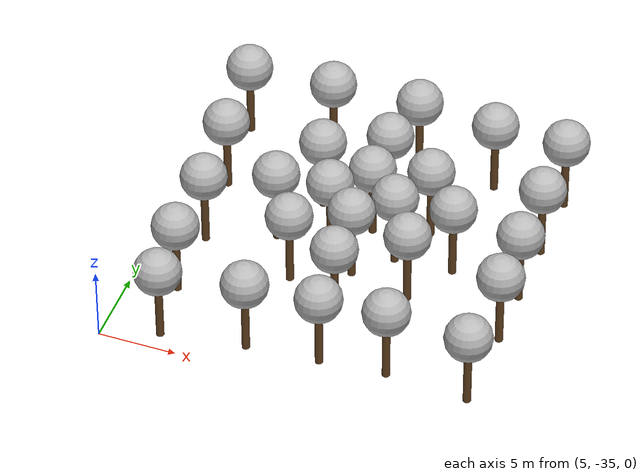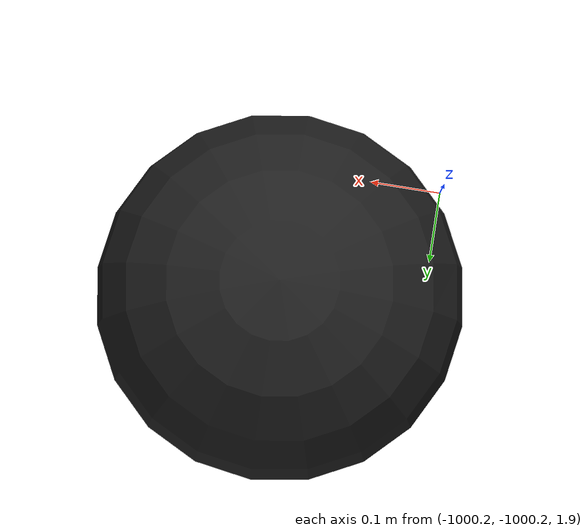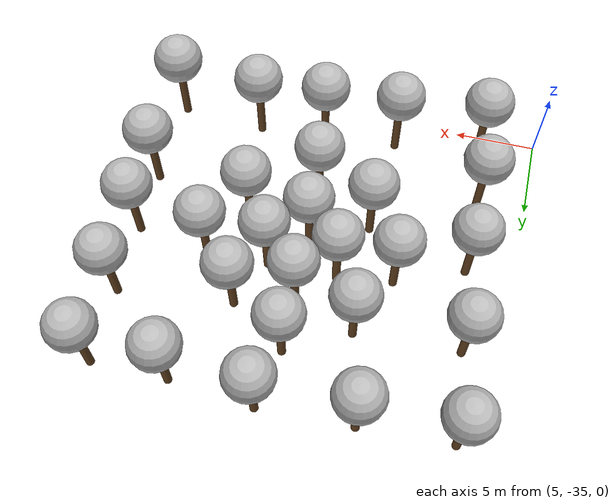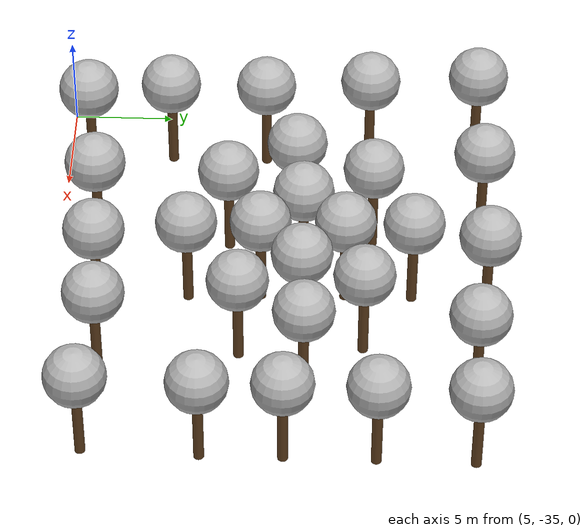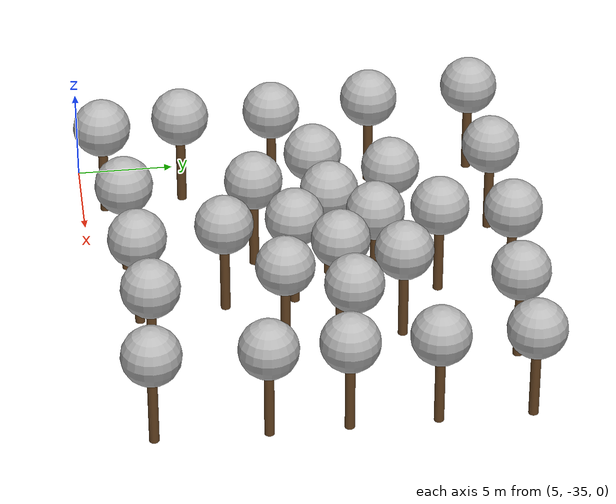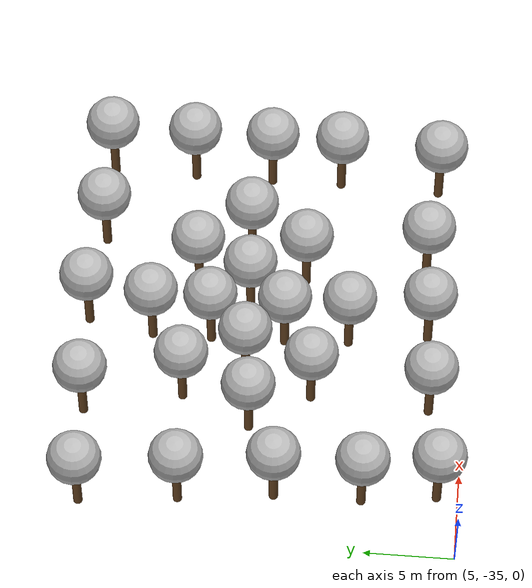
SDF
<sdf version="1.7">
 <world name="default">
  <plugin name="mrs_gazebo_static_transform_republisher_plugin" filename="libMrsGazeboCommonResources_StaticTransformRepublisher.so"/>
  <spherical_coordinates>
   <surface_model>EARTH_WGS84</surface_model>
   <latitude_deg>47.3977</latitude_deg>
   <longitude_deg>8.54559</longitude_deg>
   <elevation>0</elevation>
   <heading_deg>0</heading_deg>
  </spherical_coordinates>
  <physics name="default_physics" default="0" type="ode">
   <ode>
    <solver>
     <type>quick</type>
     <iters>10</iters>
     <sor>1.3</sor>
     <use_dynamic_moi_rescaling>0</use_dynamic_moi_rescaling>
    </solver>
    <constraints>
     <cfm>0</cfm>
     <erp>0.2</erp>
     <contact_max_correcting_vel>1000</contact_max_correcting_vel>
     <contact_surface_layer>0.001</contact_surface_layer>
    </constraints>
   </ode>
   <max_step_size>0.004</max_step_size>
   <real_time_factor>1</real_time_factor>
   <real_time_update_rate>250</real_time_update_rate>
  </physics>
  <scene><shadows>0</shadows><ambient>0.4 0.4 0.4 1</ambient><background>0.7 0.7 0.7 1</background></scene>
  <light name="sun" type="directional">
   <pose>0 0 1000 0.4 0.2 0</pose>
   <diffuse>1 1 1 1</diffuse>
   <specular>0.6 0.6 0.6 1</specular>
   <direction>0.1 0.1 -0.9</direction>
   <attenuation>
    <range>20</range>
    <constant>0.5</constant>
    <linear>0.01</linear>
    <quadratic>0.001</quadratic>
   </attenuation>
   <spot><inner_angle>0</inner_angle><outer_angle>0</outer_angle><falloff>0</falloff></spot>
  </light>
  <model name="the_void">
   <static>1</static>
   <link name="link">
    <pose>0 0 0.1 0 -0 0</pose>
    <visual name="the_void">
     <pose>0 0 2 0 -0 0</pose>
     <geometry><sphere><radius>0.25</radius></sphere></geometry>
     <material>
      <script><uri>file://media/materials/scripts/Gazebo.material</uri><name>Gazebo/Black</name></script>
     </material>
    </visual>
   </link>
   <pose>-1000 -1000 0 0 -0 0</pose>
  </model>
  <plugin name="mrs_gazebo_rviz_cam_synchronizer" filename="libMrsGazeboCommonResources_RvizCameraSynchronizer.so">
   <target_frame_id>gazebo_user_camera</target_frame_id>
   <world_origin_frame_id>uav1/gps_origin</world_origin_frame_id>
   <frame_to_follow>uav1</frame_to_follow>
  </plugin>
  <gravity>0 0 -9.8066</gravity>
  <magnetic_field>6e-06 2.3e-05 -4.2e-05</magnetic_field>
  <atmosphere type="adiabatic"/>
  <model name="tree_red_0">
   <static>1</static>
   <link name="link">
    <pose>0 0 0.1 0 -0 0</pose>
    <inertial>
     <mass>666</mass>
     <inertia>
      <ixx>0.0861167</ixx>
      <ixy>0</ixy>
      <ixz>0</ixz>
      <iyy>0.0861167</iyy>
      <iyz>0</iyz>
      <izz>0.0861167</izz>
     </inertia>
    </inertial>
    <collision name="collision_trunk">
     <pose>0 0 2 0 -0 0</pose>
     <geometry><cylinder><radius>0.25</radius><length>4</length></cylinder></geometry>
     <surface>
      <contact>
       <poissons_ratio>0.347</poissons_ratio>
       <elastic_modulus>8.8e+09</elastic_modulus>
       <ode><kp>100000</kp><kd>100</kd><max_vel>100</max_vel><min_depth>0.001</min_depth></ode>
      </contact>
      <friction>
       <torsional>
        <coefficient>1</coefficient>
        <use_patch_radius>0</use_patch_radius>
        <surface_radius>0.01</surface_radius>
       </torsional>
      </friction>
     </surface>
    </collision>
    <collision name="collision_treetop">
     <pose>0 0 5.2 0 -0 0</pose>
     <geometry><sphere><radius>1.5</radius></sphere></geometry>
     <surface>
      <contact>
       <poissons_ratio>0.347</poissons_ratio>
       <elastic_modulus>8.8e+09</elastic_modulus>
       <ode><kp>100000</kp><kd>100</kd><max_vel>100</max_vel><min_depth>0.001</min_depth></ode>
      </contact>
      <friction>
       <torsional>
        <coefficient>1</coefficient>
        <use_patch_radius>0</use_patch_radius>
        <surface_radius>0.01</surface_radius>
       </torsional>
      </friction>
     </surface>
    </collision>
    <visual name="trunk">
     <pose>0 0 2 0 -0 0</pose>
     <geometry><cylinder><radius>0.25</radius><length>4</length></cylinder></geometry>
     <material>
      <script>
       <uri>model://MRS_tree_simples_fire/scripts</uri>
       <uri>model://MRS_tree_simples_fire/materials/textures</uri>
       <name>MRS_tree_simples_fire/Trunk</name>
      </script>
     </material>
    </visual>
    <visual name="treetop">
     <pose>0 0 5.2 0 -0 0</pose>
     <geometry><sphere><radius>1.5</radius></sphere></geometry>
     <material>
      <script>
       <uri>model://MRS_tree_simples_fire/scripts</uri>
       <uri>model://MRS_tree_simples_fire/materials/textures</uri>
       <name>MRS_tree_simples_fire/Treetop</name>
      </script>
     </material>
    </visual>
   </link>
   <pose>17.6197 -20.6674 0 0 -0 0</pose>
  </model>
  <model name="tree_red_1">
   <static>1</static>
   <link name="link">
    <pose>0 0 0.1 0 -0 0</pose>
    <inertial>
     <mass>666</mass>
     <inertia>
      <ixx>0.0861167</ixx>
      <ixy>0</ixy>
      <ixz>0</ixz>
      <iyy>0.0861167</iyy>
      <iyz>0</iyz>
      <izz>0.0861167</izz>
     </inertia>
    </inertial>
    <collision name="collision_trunk">
     <pose>0 0 2 0 -0 0</pose>
     <geometry><cylinder><radius>0.25</radius><length>4</length></cylinder></geometry>
     <surface>
      <contact>
       <poissons_ratio>0.347</poissons_ratio>
       <elastic_modulus>8.8e+09</elastic_modulus>
       <ode><kp>100000</kp><kd>100</kd><max_vel>100</max_vel><min_depth>0.001</min_depth></ode>
      </contact>
      <friction>
       <torsional>
        <coefficient>1</coefficient>
        <use_patch_radius>0</use_patch_radius>
        <surface_radius>0.01</surface_radius>
       </torsional>
      </friction>
     </surface>
    </collision>
    <collision name="collision_treetop">
     <pose>0 0 5.2 0 -0 0</pose>
     <geometry><sphere><radius>1.5</radius></sphere></geometry>
     <surface>
      <contact>
       <poissons_ratio>0.347</poissons_ratio>
       <elastic_modulus>8.8e+09</elastic_modulus>
       <ode><kp>100000</kp><kd>100</kd><max_vel>100</max_vel><min_depth>0.001</min_depth></ode>
      </contact>
      <friction>
       <torsional>
        <coefficient>1</coefficient>
        <use_patch_radius>0</use_patch_radius>
        <surface_radius>0.01</surface_radius>
       </torsional>
      </friction>
     </surface>
    </collision>
    <visual name="trunk">
     <pose>0 0 2 0 -0 0</pose>
     <geometry><cylinder><radius>0.25</radius><length>4</length></cylinder></geometry>
     <material>
      <script>
       <uri>model://MRS_tree_simples_fire/scripts</uri>
       <uri>model://MRS_tree_simples_fire/materials/textures</uri>
       <name>MRS_tree_simples_fire/Trunk</name>
      </script>
     </material>
    </visual>
    <visual name="treetop">
     <pose>0 0 5.2 0 -0 0</pose>
     <geometry><sphere><radius>1.5</radius></sphere></geometry>
     <material>
      <script>
       <uri>model://MRS_tree_simples_fire/scripts</uri>
       <uri>model://MRS_tree_simples_fire/materials/textures</uri>
       <name>MRS_tree_simples_fire/Treetop</name>
      </script>
     </material>
    </visual>
   </link>
   <pose>19.8045 -22.7168 0 0 -0 0</pose>
  </model>
  <model name="tree_red_2">
   <static>1</static>
   <link name="link">
    <pose>0 0 0.1 0 -0 0</pose>
    <inertial>
     <mass>666</mass>
     <inertia>
      <ixx>0.0861167</ixx>
      <ixy>0</ixy>
      <ixz>0</ixz>
      <iyy>0.0861167</iyy>
      <iyz>0</iyz>
      <izz>0.0861167</izz>
     </inertia>
    </inertial>
    <collision name="collision_trunk">
     <pose>0 0 2 0 -0 0</pose>
     <geometry><cylinder><radius>0.25</radius><length>4</length></cylinder></geometry>
     <surface>
      <contact>
       <poissons_ratio>0.347</poissons_ratio>
       <elastic_modulus>8.8e+09</elastic_modulus>
       <ode><kp>100000</kp><kd>100</kd><max_vel>100</max_vel><min_depth>0.001</min_depth></ode>
      </contact>
      <friction>
       <torsional>
        <coefficient>1</coefficient>
        <use_patch_radius>0</use_patch_radius>
        <surface_radius>0.01</surface_radius>
       </torsional>
      </friction>
     </surface>
    </collision>
    <collision name="collision_treetop">
     <pose>0 0 5.2 0 -0 0</pose>
     <geometry><sphere><radius>1.5</radius></sphere></geometry>
     <surface>
      <contact>
       <poissons_ratio>0.347</poissons_ratio>
       <elastic_modulus>8.8e+09</elastic_modulus>
       <ode><kp>100000</kp><kd>100</kd><max_vel>100</max_vel><min_depth>0.001</min_depth></ode>
      </contact>
      <friction>
       <torsional>
        <coefficient>1</coefficient>
        <use_patch_radius>0</use_patch_radius>
        <surface_radius>0.01</surface_radius>
       </torsional>
      </friction>
     </surface>
    </collision>
    <visual name="trunk">
     <pose>0 0 2 0 -0 0</pose>
     <geometry><cylinder><radius>0.25</radius><length>4</length></cylinder></geometry>
     <material>
      <script>
       <uri>model://MRS_tree_simples_fire/scripts</uri>
       <uri>model://MRS_tree_simples_fire/materials/textures</uri>
       <name>MRS_tree_simples_fire/Trunk</name>
      </script>
     </material>
    </visual>
    <visual name="treetop">
     <pose>0 0 5.2 0 -0 0</pose>
     <geometry><sphere><radius>1.5</radius></sphere></geometry>
     <material>
      <script>
       <uri>model://MRS_tree_simples_fire/scripts</uri>
       <uri>model://MRS_tree_simples_fire/materials/textures</uri>
       <name>MRS_tree_simples_fire/Treetop</name>
      </script>
     </material>
    </visual>
   </link>
   <pose>17.7061 -24.7851 0 0 -0 0</pose>
  </model>
  <model name="tree_yellow">
   <static>1</static>
   <link name="link">
    <pose>0 0 0.1 0 -0 0</pose>
    <inertial>
     <mass>666</mass>
     <inertia>
      <ixx>0.0861167</ixx>
      <ixy>0</ixy>
      <ixz>0</ixz>
      <iyy>0.0861167</iyy>
      <iyz>0</iyz>
      <izz>0.0861167</izz>
     </inertia>
    </inertial>
    <collision name="collision_trunk">
     <pose>0 0 2 0 -0 0</pose>
     <geometry><cylinder><radius>0.25</radius><length>4</length></cylinder></geometry>
     <surface>
      <contact>
       <poissons_ratio>0.347</poissons_ratio>
       <elastic_modulus>8.8e+09</elastic_modulus>
       <ode><kp>100000</kp><kd>100</kd><max_vel>100</max_vel><min_depth>0.001</min_depth></ode>
      </contact>
      <friction>
       <torsional>
        <coefficient>1</coefficient>
        <use_patch_radius>0</use_patch_radius>
        <surface_radius>0.01</surface_radius>
       </torsional>
      </friction>
     </surface>
    </collision>
    <collision name="collision_treetop">
     <pose>0 0 5.2 0 -0 0</pose>
     <geometry><sphere><radius>1.5</radius></sphere></geometry>
     <surface>
      <contact>
       <poissons_ratio>0.347</poissons_ratio>
       <elastic_modulus>8.8e+09</elastic_modulus>
       <ode><kp>100000</kp><kd>100</kd><max_vel>100</max_vel><min_depth>0.001</min_depth></ode>
      </contact>
      <friction>
       <torsional>
        <coefficient>1</coefficient>
        <use_patch_radius>0</use_patch_radius>
        <surface_radius>0.01</surface_radius>
       </torsional>
      </friction>
     </surface>
    </collision>
    <visual name="trunk">
     <pose>0 0 2 0 -0 0</pose>
     <geometry><cylinder><radius>0.25</radius><length>4</length></cylinder></geometry>
     <material>
      <script>
       <uri>model://MRS_tree_simples_close/scripts</uri>
       <uri>model://MRS_tree_simples_close/materials/textures</uri>
       <name>MRS_tree_simples_close/Trunk</name>
      </script>
     </material>
    </visual>
    <visual name="treetop">
     <pose>0 0 5.2 0 -0 0</pose>
     <geometry><sphere><radius>1.5</radius></sphere></geometry>
     <material>
      <script>
       <uri>model://MRS_tree_simples_close/scripts</uri>
       <uri>model://MRS_tree_simples_close/materials/textures</uri>
       <name>MRS_tree_simples_close/Treetop</name>
      </script>
     </material>
    </visual>
   </link>
   <pose>21.1239 -19.7072 0 0 -0 0</pose>
  </model>
  <model name="tree_yellow_0">
   <static>1</static>
   <link name="link">
    <pose>0 0 0.1 0 -0 0</pose>
    <inertial>
     <mass>666</mass>
     <inertia>
      <ixx>0.0861167</ixx>
      <ixy>0</ixy>
      <ixz>0</ixz>
      <iyy>0.0861167</iyy>
      <iyz>0</iyz>
      <izz>0.0861167</izz>
     </inertia>
    </inertial>
    <collision name="collision_trunk">
     <pose>0 0 2 0 -0 0</pose>
     <geometry><cylinder><radius>0.25</radius><length>4</length></cylinder></geometry>
     <surface>
      <contact>
       <poissons_ratio>0.347</poissons_ratio>
       <elastic_modulus>8.8e+09</elastic_modulus>
       <ode><kp>100000</kp><kd>100</kd><max_vel>100</max_vel><min_depth>0.001</min_depth></ode>
      </contact>
      <friction>
       <torsional>
        <coefficient>1</coefficient>
        <use_patch_radius>0</use_patch_radius>
        <surface_radius>0.01</surface_radius>
       </torsional>
      </friction>
     </surface>
    </collision>
    <collision name="collision_treetop">
     <pose>0 0 5.2 0 -0 0</pose>
     <geometry><sphere><radius>1.5</radius></sphere></geometry>
     <surface>
      <contact>
       <poissons_ratio>0.347</poissons_ratio>
       <elastic_modulus>8.8e+09</elastic_modulus>
       <ode><kp>100000</kp><kd>100</kd><max_vel>100</max_vel><min_depth>0.001</min_depth></ode>
      </contact>
      <friction>
       <torsional>
        <coefficient>1</coefficient>
        <use_patch_radius>0</use_patch_radius>
        <surface_radius>0.01</surface_radius>
       </torsional>
      </friction>
     </surface>
    </collision>
    <visual name="trunk">
     <pose>0 0 2 0 -0 0</pose>
     <geometry><cylinder><radius>0.25</radius><length>4</length></cylinder></geometry>
     <material>
      <script>
       <uri>model://MRS_tree_simples_close/scripts</uri>
       <uri>model://MRS_tree_simples_close/materials/textures</uri>
       <name>MRS_tree_simples_close/Trunk</name>
      </script>
     </material>
    </visual>
    <visual name="treetop">
     <pose>0 0 5.2 0 -0 0</pose>
     <geometry><sphere><radius>1.5</radius></sphere></geometry>
     <material>
      <script>
       <uri>model://MRS_tree_simples_close/scripts</uri>
       <uri>model://MRS_tree_simples_close/materials/textures</uri>
       <name>MRS_tree_simples_close/Treetop</name>
      </script>
     </material>
    </visual>
   </link>
   <pose>23.5192 -22.5214 0 0 -0 0</pose>
  </model>
  <model name="tree_red_3">
   <static>1</static>
   <link name="link">
    <pose>0 0 0.1 0 -0 0</pose>
    <inertial>
     <mass>666</mass>
     <inertia>
      <ixx>0.0861167</ixx>
      <ixy>0</ixy>
      <ixz>0</ixz>
      <iyy>0.0861167</iyy>
      <iyz>0</iyz>
      <izz>0.0861167</izz>
     </inertia>
    </inertial>
    <collision name="collision_trunk">
     <pose>0 0 2 0 -0 0</pose>
     <geometry><cylinder><radius>0.25</radius><length>4</length></cylinder></geometry>
     <surface>
      <contact>
       <poissons_ratio>0.347</poissons_ratio>
       <elastic_modulus>8.8e+09</elastic_modulus>
       <ode><kp>100000</kp><kd>100</kd><max_vel>100</max_vel><min_depth>0.001</min_depth></ode>
      </contact>
      <friction>
       <torsional>
        <coefficient>1</coefficient>
        <use_patch_radius>0</use_patch_radius>
        <surface_radius>0.01</surface_radius>
       </torsional>
      </friction>
     </surface>
    </collision>
    <collision name="collision_treetop">
     <pose>0 0 5.2 0 -0 0</pose>
     <geometry><sphere><radius>1.5</radius></sphere></geometry>
     <surface>
      <contact>
       <poissons_ratio>0.347</poissons_ratio>
       <elastic_modulus>8.8e+09</elastic_modulus>
       <ode><kp>100000</kp><kd>100</kd><max_vel>100</max_vel><min_depth>0.001</min_depth></ode>
      </contact>
      <friction>
       <torsional>
        <coefficient>1</coefficient>
        <use_patch_radius>0</use_patch_radius>
        <surface_radius>0.01</surface_radius>
       </torsional>
      </friction>
     </surface>
    </collision>
    <visual name="trunk">
     <pose>0 0 2 0 -0 0</pose>
     <geometry><cylinder><radius>0.25</radius><length>4</length></cylinder></geometry>
     <material>
      <script>
       <uri>model://MRS_tree_simples_fire/scripts</uri>
       <uri>model://MRS_tree_simples_fire/materials/textures</uri>
       <name>MRS_tree_simples_fire/Trunk</name>
      </script>
     </material>
    </visual>
    <visual name="treetop">
     <pose>0 0 5.2 0 -0 0</pose>
     <geometry><sphere><radius>1.5</radius></sphere></geometry>
     <material>
      <script>
       <uri>model://MRS_tree_simples_fire/scripts</uri>
       <uri>model://MRS_tree_simples_fire/materials/textures</uri>
       <name>MRS_tree_simples_fire/Treetop</name>
      </script>
     </material>
    </visual>
   </link>
   <pose>15.5753 -22.7572 0 0 -0 0</pose>
  </model>
  <model name="tree_yellow_1">
   <static>1</static>
   <link name="link">
    <pose>0 0 0.1 0 -0 0</pose>
    <inertial>
     <mass>666</mass>
     <inertia>
      <ixx>0.0861167</ixx>
      <ixy>0</ixy>
      <ixz>0</ixz>
      <iyy>0.0861167</iyy>
      <iyz>0</iyz>
      <izz>0.0861167</izz>
     </inertia>
    </inertial>
    <collision name="collision_trunk">
     <pose>0 0 2 0 -0 0</pose>
     <geometry><cylinder><radius>0.25</radius><length>4</length></cylinder></geometry>
     <surface>
      <contact>
       <poissons_ratio>0.347</poissons_ratio>
       <elastic_modulus>8.8e+09</elastic_modulus>
       <ode><kp>100000</kp><kd>100</kd><max_vel>100</max_vel><min_depth>0.001</min_depth></ode>
      </contact>
      <friction>
       <torsional>
        <coefficient>1</coefficient>
        <use_patch_radius>0</use_patch_radius>
        <surface_radius>0.01</surface_radius>
       </torsional>
      </friction>
     </surface>
    </collision>
    <collision name="collision_treetop">
     <pose>0 0 5.2 0 -0 0</pose>
     <geometry><sphere><radius>1.5</radius></sphere></geometry>
     <surface>
      <contact>
       <poissons_ratio>0.347</poissons_ratio>
       <elastic_modulus>8.8e+09</elastic_modulus>
       <ode><kp>100000</kp><kd>100</kd><max_vel>100</max_vel><min_depth>0.001</min_depth></ode>
      </contact>
      <friction>
       <torsional>
        <coefficient>1</coefficient>
        <use_patch_radius>0</use_patch_radius>
        <surface_radius>0.01</surface_radius>
       </torsional>
      </friction>
     </surface>
    </collision>
    <visual name="trunk">
     <pose>0 0 2 0 -0 0</pose>
     <geometry><cylinder><radius>0.25</radius><length>4</length></cylinder></geometry>
     <material>
      <script>
       <uri>model://MRS_tree_simples_close/scripts</uri>
       <uri>model://MRS_tree_simples_close/materials/textures</uri>
       <name>MRS_tree_simples_close/Trunk</name>
      </script>
     </material>
    </visual>
    <visual name="treetop">
     <pose>0 0 5.2 0 -0 0</pose>
     <geometry><sphere><radius>1.5</radius></sphere></geometry>
     <material>
      <script>
       <uri>model://MRS_tree_simples_close/scripts</uri>
       <uri>model://MRS_tree_simples_close/materials/textures</uri>
       <name>MRS_tree_simples_close/Treetop</name>
      </script>
     </material>
    </visual>
   </link>
   <pose>12.1813 -23.1782 0 0 -0 0</pose>
  </model>
  <model name="tree_yellow_2">
   <static>1</static>
   <link name="link">
    <pose>0 0 0.1 0 -0 0</pose>
    <inertial>
     <mass>666</mass>
     <inertia>
      <ixx>0.0861167</ixx>
      <ixy>0</ixy>
      <ixz>0</ixz>
      <iyy>0.0861167</iyy>
      <iyz>0</iyz>
      <izz>0.0861167</izz>
     </inertia>
    </inertial>
    <collision name="collision_trunk">
     <pose>0 0 2 0 -0 0</pose>
     <geometry><cylinder><radius>0.25</radius><length>4</length></cylinder></geometry>
     <surface>
      <contact>
       <poissons_ratio>0.347</poissons_ratio>
       <elastic_modulus>8.8e+09</elastic_modulus>
       <ode><kp>100000</kp><kd>100</kd><max_vel>100</max_vel><min_depth>0.001</min_depth></ode>
      </contact>
      <friction>
       <torsional>
        <coefficient>1</coefficient>
        <use_patch_radius>0</use_patch_radius>
        <surface_radius>0.01</surface_radius>
       </torsional>
      </friction>
     </surface>
    </collision>
    <collision name="collision_treetop">
     <pose>0 0 5.2 0 -0 0</pose>
     <geometry><sphere><radius>1.5</radius></sphere></geometry>
     <surface>
      <contact>
       <poissons_ratio>0.347</poissons_ratio>
       <elastic_modulus>8.8e+09</elastic_modulus>
       <ode><kp>100000</kp><kd>100</kd><max_vel>100</max_vel><min_depth>0.001</min_depth></ode>
      </contact>
      <friction>
       <torsional>
        <coefficient>1</coefficient>
        <use_patch_radius>0</use_patch_radius>
        <surface_radius>0.01</surface_radius>
       </torsional>
      </friction>
     </surface>
    </collision>
    <visual name="trunk">
     <pose>0 0 2 0 -0 0</pose>
     <geometry><cylinder><radius>0.25</radius><length>4</length></cylinder></geometry>
     <material>
      <script>
       <uri>model://MRS_tree_simples_close/scripts</uri>
       <uri>model://MRS_tree_simples_close/materials/textures</uri>
       <name>MRS_tree_simples_close/Trunk</name>
      </script>
     </material>
    </visual>
    <visual name="treetop">
     <pose>0 0 5.2 0 -0 0</pose>
     <geometry><sphere><radius>1.5</radius></sphere></geometry>
     <material>
      <script>
       <uri>model://MRS_tree_simples_close/scripts</uri>
       <uri>model://MRS_tree_simples_close/materials/textures</uri>
       <name>MRS_tree_simples_close/Treetop</name>
      </script>
     </material>
    </visual>
   </link>
   <pose>17.62 -17.3731 0 0 -0 0</pose>
  </model>
  <model name="tree_yellow_3">
   <static>1</static>
   <link name="link">
    <pose>0 0 0.1 0 -0 0</pose>
    <inertial>
     <mass>666</mass>
     <inertia>
      <ixx>0.0861167</ixx>
      <ixy>0</ixy>
      <ixz>0</ixz>
      <iyy>0.0861167</iyy>
      <iyz>0</iyz>
      <izz>0.0861167</izz>
     </inertia>
    </inertial>
    <collision name="collision_trunk">
     <pose>0 0 2 0 -0 0</pose>
     <geometry><cylinder><radius>0.25</radius><length>4</length></cylinder></geometry>
     <surface>
      <contact>
       <poissons_ratio>0.347</poissons_ratio>
       <elastic_modulus>8.8e+09</elastic_modulus>
       <ode><kp>100000</kp><kd>100</kd><max_vel>100</max_vel><min_depth>0.001</min_depth></ode>
      </contact>
      <friction>
       <torsional>
        <coefficient>1</coefficient>
        <use_patch_radius>0</use_patch_radius>
        <surface_radius>0.01</surface_radius>
       </torsional>
      </friction>
     </surface>
    </collision>
    <collision name="collision_treetop">
     <pose>0 0 5.2 0 -0 0</pose>
     <geometry><sphere><radius>1.5</radius></sphere></geometry>
     <surface>
      <contact>
       <poissons_ratio>0.347</poissons_ratio>
       <elastic_modulus>8.8e+09</elastic_modulus>
       <ode><kp>100000</kp><kd>100</kd><max_vel>100</max_vel><min_depth>0.001</min_depth></ode>
      </contact>
      <friction>
       <torsional>
        <coefficient>1</coefficient>
        <use_patch_radius>0</use_patch_radius>
        <surface_radius>0.01</surface_radius>
       </torsional>
      </friction>
     </surface>
    </collision>
    <visual name="trunk">
     <pose>0 0 2 0 -0 0</pose>
     <geometry><cylinder><radius>0.25</radius><length>4</length></cylinder></geometry>
     <material>
      <script>
       <uri>model://MRS_tree_simples_close/scripts</uri>
       <uri>model://MRS_tree_simples_close/materials/textures</uri>
       <name>MRS_tree_simples_close/Trunk</name>
      </script>
     </material>
    </visual>
    <visual name="treetop">
     <pose>0 0 5.2 0 -0 0</pose>
     <geometry><sphere><radius>1.5</radius></sphere></geometry>
     <material>
      <script>
       <uri>model://MRS_tree_simples_close/scripts</uri>
       <uri>model://MRS_tree_simples_close/materials/textures</uri>
       <name>MRS_tree_simples_close/Treetop</name>
      </script>
     </material>
    </visual>
   </link>
   <pose>21.673 -25.7191 0 0 -0 0</pose>
  </model>
  <model name="tree_yellow_4">
   <static>1</static>
   <link name="link">
    <pose>0 0 0.1 0 -0 0</pose>
    <inertial>
     <mass>666</mass>
     <inertia>
      <ixx>0.0861167</ixx>
      <ixy>0</ixy>
      <ixz>0</ixz>
      <iyy>0.0861167</iyy>
      <iyz>0</iyz>
      <izz>0.0861167</izz>
     </inertia>
    </inertial>
    <collision name="collision_trunk">
     <pose>0 0 2 0 -0 0</pose>
     <geometry><cylinder><radius>0.25</radius><length>4</length></cylinder></geometry>
     <surface>
      <contact>
       <poissons_ratio>0.347</poissons_ratio>
       <elastic_modulus>8.8e+09</elastic_modulus>
       <ode><kp>100000</kp><kd>100</kd><max_vel>100</max_vel><min_depth>0.001</min_depth></ode>
      </contact>
      <friction>
       <torsional>
        <coefficient>1</coefficient>
        <use_patch_radius>0</use_patch_radius>
        <surface_radius>0.01</surface_radius>
       </torsional>
      </friction>
     </surface>
    </collision>
    <collision name="collision_treetop">
     <pose>0 0 5.2 0 -0 0</pose>
     <geometry><sphere><radius>1.5</radius></sphere></geometry>
     <surface>
      <contact>
       <poissons_ratio>0.347</poissons_ratio>
       <elastic_modulus>8.8e+09</elastic_modulus>
       <ode><kp>100000</kp><kd>100</kd><max_vel>100</max_vel><min_depth>0.001</min_depth></ode>
      </contact>
      <friction>
       <torsional>
        <coefficient>1</coefficient>
        <use_patch_radius>0</use_patch_radius>
        <surface_radius>0.01</surface_radius>
       </torsional>
      </friction>
     </surface>
    </collision>
    <visual name="trunk">
     <pose>0 0 2 0 -0 0</pose>
     <geometry><cylinder><radius>0.25</radius><length>4</length></cylinder></geometry>
     <material>
      <script>
       <uri>model://MRS_tree_simples_close/scripts</uri>
       <uri>model://MRS_tree_simples_close/materials/textures</uri>
       <name>MRS_tree_simples_close/Trunk</name>
      </script>
     </material>
    </visual>
    <visual name="treetop">
     <pose>0 0 5.2 0 -0 0</pose>
     <geometry><sphere><radius>1.5</radius></sphere></geometry>
     <material>
      <script>
       <uri>model://MRS_tree_simples_close/scripts</uri>
       <uri>model://MRS_tree_simples_close/materials/textures</uri>
       <name>MRS_tree_simples_close/Treetop</name>
      </script>
     </material>
    </visual>
   </link>
   <pose>13.8665 -19.3681 0 0 -0 0</pose>
  </model>
  <model name="tree_yellow_5">
   <static>1</static>
   <link name="link">
    <pose>0 0 0.1 0 -0 0</pose>
    <inertial>
     <mass>666</mass>
     <inertia>
      <ixx>0.0861167</ixx>
      <ixy>0</ixy>
      <ixz>0</ixz>
      <iyy>0.0861167</iyy>
      <iyz>0</iyz>
      <izz>0.0861167</izz>
     </inertia>
    </inertial>
    <collision name="collision_trunk">
     <pose>0 0 2 0 -0 0</pose>
     <geometry><cylinder><radius>0.25</radius><length>4</length></cylinder></geometry>
     <surface>
      <contact>
       <poissons_ratio>0.347</poissons_ratio>
       <elastic_modulus>8.8e+09</elastic_modulus>
       <ode><kp>100000</kp><kd>100</kd><max_vel>100</max_vel><min_depth>0.001</min_depth></ode>
      </contact>
      <friction>
       <torsional>
        <coefficient>1</coefficient>
        <use_patch_radius>0</use_patch_radius>
        <surface_radius>0.01</surface_radius>
       </torsional>
      </friction>
     </surface>
    </collision>
    <collision name="collision_treetop">
     <pose>0 0 5.2 0 -0 0</pose>
     <geometry><sphere><radius>1.5</radius></sphere></geometry>
     <surface>
      <contact>
       <poissons_ratio>0.347</poissons_ratio>
       <elastic_modulus>8.8e+09</elastic_modulus>
       <ode><kp>100000</kp><kd>100</kd><max_vel>100</max_vel><min_depth>0.001</min_depth></ode>
      </contact>
      <friction>
       <torsional>
        <coefficient>1</coefficient>
        <use_patch_radius>0</use_patch_radius>
        <surface_radius>0.01</surface_radius>
       </torsional>
      </friction>
     </surface>
    </collision>
    <visual name="trunk">
     <pose>0 0 2 0 -0 0</pose>
     <geometry><cylinder><radius>0.25</radius><length>4</length></cylinder></geometry>
     <material>
      <script>
       <uri>model://MRS_tree_simples_close/scripts</uri>
       <uri>model://MRS_tree_simples_close/materials/textures</uri>
       <name>MRS_tree_simples_close/Trunk</name>
      </script>
     </material>
    </visual>
    <visual name="treetop">
     <pose>0 0 5.2 0 -0 0</pose>
     <geometry><sphere><radius>1.5</radius></sphere></geometry>
     <material>
      <script>
       <uri>model://MRS_tree_simples_close/scripts</uri>
       <uri>model://MRS_tree_simples_close/materials/textures</uri>
       <name>MRS_tree_simples_close/Treetop</name>
      </script>
     </material>
    </visual>
   </link>
   <pose>17.8933 -28.3603 0 0 -0 0</pose>
  </model>
  <model name="tree_yellow_6">
   <static>1</static>
   <link name="link">
    <pose>0 0 0.1 0 -0 0</pose>
    <inertial>
     <mass>666</mass>
     <inertia>
      <ixx>0.0861167</ixx>
      <ixy>0</ixy>
      <ixz>0</ixz>
      <iyy>0.0861167</iyy>
      <iyz>0</iyz>
      <izz>0.0861167</izz>
     </inertia>
    </inertial>
    <collision name="collision_trunk">
     <pose>0 0 2 0 -0 0</pose>
     <geometry><cylinder><radius>0.25</radius><length>4</length></cylinder></geometry>
     <surface>
      <contact>
       <poissons_ratio>0.347</poissons_ratio>
       <elastic_modulus>8.8e+09</elastic_modulus>
       <ode><kp>100000</kp><kd>100</kd><max_vel>100</max_vel><min_depth>0.001</min_depth></ode>
      </contact>
      <friction>
       <torsional>
        <coefficient>1</coefficient>
        <use_patch_radius>0</use_patch_radius>
        <surface_radius>0.01</surface_radius>
       </torsional>
      </friction>
     </surface>
    </collision>
    <collision name="collision_treetop">
     <pose>0 0 5.2 0 -0 0</pose>
     <geometry><sphere><radius>1.5</radius></sphere></geometry>
     <surface>
      <contact>
       <poissons_ratio>0.347</poissons_ratio>
       <elastic_modulus>8.8e+09</elastic_modulus>
       <ode><kp>100000</kp><kd>100</kd><max_vel>100</max_vel><min_depth>0.001</min_depth></ode>
      </contact>
      <friction>
       <torsional>
        <coefficient>1</coefficient>
        <use_patch_radius>0</use_patch_radius>
        <surface_radius>0.01</surface_radius>
       </torsional>
      </friction>
     </surface>
    </collision>
    <visual name="trunk">
     <pose>0 0 2 0 -0 0</pose>
     <geometry><cylinder><radius>0.25</radius><length>4</length></cylinder></geometry>
     <material>
      <script>
       <uri>model://MRS_tree_simples_close/scripts</uri>
       <uri>model://MRS_tree_simples_close/materials/textures</uri>
       <name>MRS_tree_simples_close/Trunk</name>
      </script>
     </material>
    </visual>
    <visual name="treetop">
     <pose>0 0 5.2 0 -0 0</pose>
     <geometry><sphere><radius>1.5</radius></sphere></geometry>
     <material>
      <script>
       <uri>model://MRS_tree_simples_close/scripts</uri>
       <uri>model://MRS_tree_simples_close/materials/textures</uri>
       <name>MRS_tree_simples_close/Treetop</name>
      </script>
     </material>
    </visual>
   </link>
   <pose>14.2717 -26.4887 0 0 -0 0</pose>
  </model>
  <model name="tree_green">
   <static>1</static>
   <link name="link">
    <pose>0 0 0.1 0 -0 0</pose>
    <inertial>
     <mass>666</mass>
     <inertia>
      <ixx>0.0861167</ixx>
      <ixy>0</ixy>
      <ixz>0</ixz>
      <iyy>0.0861167</iyy>
      <iyz>0</iyz>
      <izz>0.0861167</izz>
     </inertia>
    </inertial>
    <collision name="collision_trunk">
     <pose>0 0 2 0 -0 0</pose>
     <geometry><cylinder><radius>0.25</radius><length>4</length></cylinder></geometry>
     <surface>
      <contact>
       <poissons_ratio>0.347</poissons_ratio>
       <elastic_modulus>8.8e+09</elastic_modulus>
       <ode><kp>100000</kp><kd>100</kd><max_vel>100</max_vel><min_depth>0.001</min_depth></ode>
      </contact>
      <friction>
       <torsional>
        <coefficient>1</coefficient>
        <use_patch_radius>0</use_patch_radius>
        <surface_radius>0.01</surface_radius>
       </torsional>
      </friction>
     </surface>
    </collision>
    <collision name="collision_treetop">
     <pose>0 0 5.2 0 -0 0</pose>
     <geometry><sphere><radius>1.5</radius></sphere></geometry>
     <surface>
      <contact>
       <poissons_ratio>0.347</poissons_ratio>
       <elastic_modulus>8.8e+09</elastic_modulus>
       <ode><kp>100000</kp><kd>100</kd><max_vel>100</max_vel><min_depth>0.001</min_depth></ode>
      </contact>
      <friction>
       <torsional>
        <coefficient>1</coefficient>
        <use_patch_radius>0</use_patch_radius>
        <surface_radius>0.01</surface_radius>
       </torsional>
      </friction>
     </surface>
    </collision>
    <visual name="trunk">
     <pose>0 0 2 0 -0 0</pose>
     <geometry><cylinder><radius>0.25</radius><length>4</length></cylinder></geometry>
     <material>
      <script>
       <uri>model://MRS_tree_simple/scripts</uri>
       <uri>model://MRS_tree_simple/materials/textures</uri>
       <name>MRS_tree_simple/Trunk</name>
      </script>
     </material>
    </visual>
    <visual name="treetop">
     <pose>0 0 5.2 0 -0 0</pose>
     <geometry><sphere><radius>1.5</radius></sphere></geometry>
     <material>
      <script>
       <uri>model://MRS_tree_simple/scripts</uri>
       <uri>model://MRS_tree_simple/materials/textures</uri>
       <name>MRS_tree_simple/Treetop</name>
      </script>
     </material>
    </visual>
   </link>
   <pose>18.3034 -13.7371 0 0 -0 0</pose>
  </model>
  <model name="tree_green_0">
   <static>1</static>
   <link name="link">
    <pose>0 0 0.1 0 -0 0</pose>
    <inertial>
     <mass>666</mass>
     <inertia>
      <ixx>0.0861167</ixx>
      <ixy>0</ixy>
      <ixz>0</ixz>
      <iyy>0.0861167</iyy>
      <iyz>0</iyz>
      <izz>0.0861167</izz>
     </inertia>
    </inertial>
    <collision name="collision_trunk">
     <pose>0 0 2 0 -0 0</pose>
     <geometry><cylinder><radius>0.25</radius><length>4</length></cylinder></geometry>
     <surface>
      <contact>
       <poissons_ratio>0.347</poissons_ratio>
       <elastic_modulus>8.8e+09</elastic_modulus>
       <ode><kp>100000</kp><kd>100</kd><max_vel>100</max_vel><min_depth>0.001</min_depth></ode>
      </contact>
      <friction>
       <torsional>
        <coefficient>1</coefficient>
        <use_patch_radius>0</use_patch_radius>
        <surface_radius>0.01</surface_radius>
       </torsional>
      </friction>
     </surface>
    </collision>
    <collision name="collision_treetop">
     <pose>0 0 5.2 0 -0 0</pose>
     <geometry><sphere><radius>1.5</radius></sphere></geometry>
     <surface>
      <contact>
       <poissons_ratio>0.347</poissons_ratio>
       <elastic_modulus>8.8e+09</elastic_modulus>
       <ode><kp>100000</kp><kd>100</kd><max_vel>100</max_vel><min_depth>0.001</min_depth></ode>
      </contact>
      <friction>
       <torsional>
        <coefficient>1</coefficient>
        <use_patch_radius>0</use_patch_radius>
        <surface_radius>0.01</surface_radius>
       </torsional>
      </friction>
     </surface>
    </collision>
    <visual name="trunk">
     <pose>0 0 2 0 -0 0</pose>
     <geometry><cylinder><radius>0.25</radius><length>4</length></cylinder></geometry>
     <material>
      <script>
       <uri>model://MRS_tree_simple/scripts</uri>
       <uri>model://MRS_tree_simple/materials/textures</uri>
       <name>MRS_tree_simple/Trunk</name>
      </script>
     </material>
    </visual>
    <visual name="treetop">
     <pose>0 0 5.2 0 -0 0</pose>
     <geometry><sphere><radius>1.5</radius></sphere></geometry>
     <material>
      <script>
       <uri>model://MRS_tree_simple/scripts</uri>
       <uri>model://MRS_tree_simple/materials/textures</uri>
       <name>MRS_tree_simple/Treetop</name>
      </script>
     </material>
    </visual>
   </link>
   <pose>23.4977 -14.2435 0 0 -0 0</pose>
  </model>
  <model name="tree_green_1">
   <static>1</static>
   <link name="link">
    <pose>0 0 0.1 0 -0 0</pose>
    <inertial>
     <mass>666</mass>
     <inertia>
      <ixx>0.0861167</ixx>
      <ixy>0</ixy>
      <ixz>0</ixz>
      <iyy>0.0861167</iyy>
      <iyz>0</iyz>
      <izz>0.0861167</izz>
     </inertia>
    </inertial>
    <collision name="collision_trunk">
     <pose>0 0 2 0 -0 0</pose>
     <geometry><cylinder><radius>0.25</radius><length>4</length></cylinder></geometry>
     <surface>
      <contact>
       <poissons_ratio>0.347</poissons_ratio>
       <elastic_modulus>8.8e+09</elastic_modulus>
       <ode><kp>100000</kp><kd>100</kd><max_vel>100</max_vel><min_depth>0.001</min_depth></ode>
      </contact>
      <friction>
       <torsional>
        <coefficient>1</coefficient>
        <use_patch_radius>0</use_patch_radius>
        <surface_radius>0.01</surface_radius>
       </torsional>
      </friction>
     </surface>
    </collision>
    <collision name="collision_treetop">
     <pose>0 0 5.2 0 -0 0</pose>
     <geometry><sphere><radius>1.5</radius></sphere></geometry>
     <surface>
      <contact>
       <poissons_ratio>0.347</poissons_ratio>
       <elastic_modulus>8.8e+09</elastic_modulus>
       <ode><kp>100000</kp><kd>100</kd><max_vel>100</max_vel><min_depth>0.001</min_depth></ode>
      </contact>
      <friction>
       <torsional>
        <coefficient>1</coefficient>
        <use_patch_radius>0</use_patch_radius>
        <surface_radius>0.01</surface_radius>
       </torsional>
      </friction>
     </surface>
    </collision>
    <visual name="trunk">
     <pose>0 0 2 0 -0 0</pose>
     <geometry><cylinder><radius>0.25</radius><length>4</length></cylinder></geometry>
     <material>
      <script>
       <uri>model://MRS_tree_simple/scripts</uri>
       <uri>model://MRS_tree_simple/materials/textures</uri>
       <name>MRS_tree_simple/Trunk</name>
      </script>
     </material>
    </visual>
    <visual name="treetop">
     <pose>0 0 5.2 0 -0 0</pose>
     <geometry><sphere><radius>1.5</radius></sphere></geometry>
     <material>
      <script>
       <uri>model://MRS_tree_simple/scripts</uri>
       <uri>model://MRS_tree_simple/materials/textures</uri>
       <name>MRS_tree_simple/Treetop</name>
      </script>
     </material>
    </visual>
   </link>
   <pose>28.1665 -14.2881 0 0 -0 0</pose>
  </model>
  <model name="tree_green_2">
   <static>1</static>
   <link name="link">
    <pose>0 0 0.1 0 -0 0</pose>
    <inertial>
     <mass>666</mass>
     <inertia>
      <ixx>0.0861167</ixx>
      <ixy>0</ixy>
      <ixz>0</ixz>
      <iyy>0.0861167</iyy>
      <iyz>0</iyz>
      <izz>0.0861167</izz>
     </inertia>
    </inertial>
    <collision name="collision_trunk">
     <pose>0 0 2 0 -0 0</pose>
     <geometry><cylinder><radius>0.25</radius><length>4</length></cylinder></geometry>
     <surface>
      <contact>
       <poissons_ratio>0.347</poissons_ratio>
       <elastic_modulus>8.8e+09</elastic_modulus>
       <ode><kp>100000</kp><kd>100</kd><max_vel>100</max_vel><min_depth>0.001</min_depth></ode>
      </contact>
      <friction>
       <torsional>
        <coefficient>1</coefficient>
        <use_patch_radius>0</use_patch_radius>
        <surface_radius>0.01</surface_radius>
       </torsional>
      </friction>
     </surface>
    </collision>
    <collision name="collision_treetop">
     <pose>0 0 5.2 0 -0 0</pose>
     <geometry><sphere><radius>1.5</radius></sphere></geometry>
     <surface>
      <contact>
       <poissons_ratio>0.347</poissons_ratio>
       <elastic_modulus>8.8e+09</elastic_modulus>
       <ode><kp>100000</kp><kd>100</kd><max_vel>100</max_vel><min_depth>0.001</min_depth></ode>
      </contact>
      <friction>
       <torsional>
        <coefficient>1</coefficient>
        <use_patch_radius>0</use_patch_radius>
        <surface_radius>0.01</surface_radius>
       </torsional>
      </friction>
     </surface>
    </collision>
    <visual name="trunk">
     <pose>0 0 2 0 -0 0</pose>
     <geometry><cylinder><radius>0.25</radius><length>4</length></cylinder></geometry>
     <material>
      <script>
       <uri>model://MRS_tree_simple/scripts</uri>
       <uri>model://MRS_tree_simple/materials/textures</uri>
       <name>MRS_tree_simple/Trunk</name>
      </script>
     </material>
    </visual>
    <visual name="treetop">
     <pose>0 0 5.2 0 -0 0</pose>
     <geometry><sphere><radius>1.5</radius></sphere></geometry>
     <material>
      <script>
       <uri>model://MRS_tree_simple/scripts</uri>
       <uri>model://MRS_tree_simple/materials/textures</uri>
       <name>MRS_tree_simple/Treetop</name>
      </script>
     </material>
    </visual>
   </link>
   <pose>28.1205 -23.3465 0 0 -0 0</pose>
  </model>
  <model name="tree_green_3">
   <static>1</static>
   <link name="link">
    <pose>0 0 0.1 0 -0 0</pose>
    <inertial>
     <mass>666</mass>
     <inertia>
      <ixx>0.0861167</ixx>
      <ixy>0</ixy>
      <ixz>0</ixz>
      <iyy>0.0861167</iyy>
      <iyz>0</iyz>
      <izz>0.0861167</izz>
     </inertia>
    </inertial>
    <collision name="collision_trunk">
     <pose>0 0 2 0 -0 0</pose>
     <geometry><cylinder><radius>0.25</radius><length>4</length></cylinder></geometry>
     <surface>
      <contact>
       <poissons_ratio>0.347</poissons_ratio>
       <elastic_modulus>8.8e+09</elastic_modulus>
       <ode><kp>100000</kp><kd>100</kd><max_vel>100</max_vel><min_depth>0.001</min_depth></ode>
      </contact>
      <friction>
       <torsional>
        <coefficient>1</coefficient>
        <use_patch_radius>0</use_patch_radius>
        <surface_radius>0.01</surface_radius>
       </torsional>
      </friction>
     </surface>
    </collision>
    <collision name="collision_treetop">
     <pose>0 0 5.2 0 -0 0</pose>
     <geometry><sphere><radius>1.5</radius></sphere></geometry>
     <surface>
      <contact>
       <poissons_ratio>0.347</poissons_ratio>
       <elastic_modulus>8.8e+09</elastic_modulus>
       <ode><kp>100000</kp><kd>100</kd><max_vel>100</max_vel><min_depth>0.001</min_depth></ode>
      </contact>
      <friction>
       <torsional>
        <coefficient>1</coefficient>
        <use_patch_radius>0</use_patch_radius>
        <surface_radius>0.01</surface_radius>
       </torsional>
      </friction>
     </surface>
    </collision>
    <visual name="trunk">
     <pose>0 0 2 0 -0 0</pose>
     <geometry><cylinder><radius>0.25</radius><length>4</length></cylinder></geometry>
     <material>
      <script>
       <uri>model://MRS_tree_simple/scripts</uri>
       <uri>model://MRS_tree_simple/materials/textures</uri>
       <name>MRS_tree_simple/Trunk</name>
      </script>
     </material>
    </visual>
    <visual name="treetop">
     <pose>0 0 5.2 0 -0 0</pose>
     <geometry><sphere><radius>1.5</radius></sphere></geometry>
     <material>
      <script>
       <uri>model://MRS_tree_simple/scripts</uri>
       <uri>model://MRS_tree_simple/materials/textures</uri>
       <name>MRS_tree_simple/Treetop</name>
      </script>
     </material>
    </visual>
   </link>
   <pose>28.149 -27.2805 0 0 -0 0</pose>
  </model>
  <model name="tree_green_4">
   <static>1</static>
   <link name="link">
    <pose>0 0 0.1 0 -0 0</pose>
    <inertial>
     <mass>666</mass>
     <inertia>
      <ixx>0.0861167</ixx>
      <ixy>0</ixy>
      <ixz>0</ixz>
      <iyy>0.0861167</iyy>
      <iyz>0</iyz>
      <izz>0.0861167</izz>
     </inertia>
    </inertial>
    <collision name="collision_trunk">
     <pose>0 0 2 0 -0 0</pose>
     <geometry><cylinder><radius>0.25</radius><length>4</length></cylinder></geometry>
     <surface>
      <contact>
       <poissons_ratio>0.347</poissons_ratio>
       <elastic_modulus>8.8e+09</elastic_modulus>
       <ode><kp>100000</kp><kd>100</kd><max_vel>100</max_vel><min_depth>0.001</min_depth></ode>
      </contact>
      <friction>
       <torsional>
        <coefficient>1</coefficient>
        <use_patch_radius>0</use_patch_radius>
        <surface_radius>0.01</surface_radius>
       </torsional>
      </friction>
     </surface>
    </collision>
    <collision name="collision_treetop">
     <pose>0 0 5.2 0 -0 0</pose>
     <geometry><sphere><radius>1.5</radius></sphere></geometry>
     <surface>
      <contact>
       <poissons_ratio>0.347</poissons_ratio>
       <elastic_modulus>8.8e+09</elastic_modulus>
       <ode><kp>100000</kp><kd>100</kd><max_vel>100</max_vel><min_depth>0.001</min_depth></ode>
      </contact>
      <friction>
       <torsional>
        <coefficient>1</coefficient>
        <use_patch_radius>0</use_patch_radius>
        <surface_radius>0.01</surface_radius>
       </torsional>
      </friction>
     </surface>
    </collision>
    <visual name="trunk">
     <pose>0 0 2 0 -0 0</pose>
     <geometry><cylinder><radius>0.25</radius><length>4</length></cylinder></geometry>
     <material>
      <script>
       <uri>model://MRS_tree_simple/scripts</uri>
       <uri>model://MRS_tree_simple/materials/textures</uri>
       <name>MRS_tree_simple/Trunk</name>
      </script>
     </material>
    </visual>
    <visual name="treetop">
     <pose>0 0 5.2 0 -0 0</pose>
     <geometry><sphere><radius>1.5</radius></sphere></geometry>
     <material>
      <script>
       <uri>model://MRS_tree_simple/scripts</uri>
       <uri>model://MRS_tree_simple/materials/textures</uri>
       <name>MRS_tree_simple/Treetop</name>
      </script>
     </material>
    </visual>
   </link>
   <pose>27.9805 -32.876 0 0 -0 0</pose>
  </model>
  <model name="tree_green_5">
   <static>1</static>
   <link name="link">
    <pose>0 0 0.1 0 -0 0</pose>
    <inertial>
     <mass>666</mass>
     <inertia>
      <ixx>0.0861167</ixx>
      <ixy>0</ixy>
      <ixz>0</ixz>
      <iyy>0.0861167</iyy>
      <iyz>0</iyz>
      <izz>0.0861167</izz>
     </inertia>
    </inertial>
    <collision name="collision_trunk">
     <pose>0 0 2 0 -0 0</pose>
     <geometry><cylinder><radius>0.25</radius><length>4</length></cylinder></geometry>
     <surface>
      <contact>
       <poissons_ratio>0.347</poissons_ratio>
       <elastic_modulus>8.8e+09</elastic_modulus>
       <ode><kp>100000</kp><kd>100</kd><max_vel>100</max_vel><min_depth>0.001</min_depth></ode>
      </contact>
      <friction>
       <torsional>
        <coefficient>1</coefficient>
        <use_patch_radius>0</use_patch_radius>
        <surface_radius>0.01</surface_radius>
       </torsional>
      </friction>
     </surface>
    </collision>
    <collision name="collision_treetop">
     <pose>0 0 5.2 0 -0 0</pose>
     <geometry><sphere><radius>1.5</radius></sphere></geometry>
     <surface>
      <contact>
       <poissons_ratio>0.347</poissons_ratio>
       <elastic_modulus>8.8e+09</elastic_modulus>
       <ode><kp>100000</kp><kd>100</kd><max_vel>100</max_vel><min_depth>0.001</min_depth></ode>
      </contact>
      <friction>
       <torsional>
        <coefficient>1</coefficient>
        <use_patch_radius>0</use_patch_radius>
        <surface_radius>0.01</surface_radius>
       </torsional>
      </friction>
     </surface>
    </collision>
    <visual name="trunk">
     <pose>0 0 2 0 -0 0</pose>
     <geometry><cylinder><radius>0.25</radius><length>4</length></cylinder></geometry>
     <material>
      <script>
       <uri>model://MRS_tree_simple/scripts</uri>
       <uri>model://MRS_tree_simple/materials/textures</uri>
       <name>MRS_tree_simple/Trunk</name>
      </script>
     </material>
    </visual>
    <visual name="treetop">
     <pose>0 0 5.2 0 -0 0</pose>
     <geometry><sphere><radius>1.5</radius></sphere></geometry>
     <material>
      <script>
       <uri>model://MRS_tree_simple/scripts</uri>
       <uri>model://MRS_tree_simple/materials/textures</uri>
       <name>MRS_tree_simple/Treetop</name>
      </script>
     </material>
    </visual>
   </link>
   <pose>22.6912 -32.4673 0 0 -0 0</pose>
  </model>
  <model name="tree_green_6">
   <static>1</static>
   <link name="link">
    <pose>0 0 0.1 0 -0 0</pose>
    <inertial>
     <mass>666</mass>
     <inertia>
      <ixx>0.0861167</ixx>
      <ixy>0</ixy>
      <ixz>0</ixz>
      <iyy>0.0861167</iyy>
      <iyz>0</iyz>
      <izz>0.0861167</izz>
     </inertia>
    </inertial>
    <collision name="collision_trunk">
     <pose>0 0 2 0 -0 0</pose>
     <geometry><cylinder><radius>0.25</radius><length>4</length></cylinder></geometry>
     <surface>
      <contact>
       <poissons_ratio>0.347</poissons_ratio>
       <elastic_modulus>8.8e+09</elastic_modulus>
       <ode><kp>100000</kp><kd>100</kd><max_vel>100</max_vel><min_depth>0.001</min_depth></ode>
      </contact>
      <friction>
       <torsional>
        <coefficient>1</coefficient>
        <use_patch_radius>0</use_patch_radius>
        <surface_radius>0.01</surface_radius>
       </torsional>
      </friction>
     </surface>
    </collision>
    <collision name="collision_treetop">
     <pose>0 0 5.2 0 -0 0</pose>
     <geometry><sphere><radius>1.5</radius></sphere></geometry>
     <surface>
      <contact>
       <poissons_ratio>0.347</poissons_ratio>
       <elastic_modulus>8.8e+09</elastic_modulus>
       <ode><kp>100000</kp><kd>100</kd><max_vel>100</max_vel><min_depth>0.001</min_depth></ode>
      </contact>
      <friction>
       <torsional>
        <coefficient>1</coefficient>
        <use_patch_radius>0</use_patch_radius>
        <surface_radius>0.01</surface_radius>
       </torsional>
      </friction>
     </surface>
    </collision>
    <visual name="trunk">
     <pose>0 0 2 0 -0 0</pose>
     <geometry><cylinder><radius>0.25</radius><length>4</length></cylinder></geometry>
     <material>
      <script>
       <uri>model://MRS_tree_simple/scripts</uri>
       <uri>model://MRS_tree_simple/materials/textures</uri>
       <name>MRS_tree_simple/Trunk</name>
      </script>
     </material>
    </visual>
    <visual name="treetop">
     <pose>0 0 5.2 0 -0 0</pose>
     <geometry><sphere><radius>1.5</radius></sphere></geometry>
     <material>
      <script>
       <uri>model://MRS_tree_simple/scripts</uri>
       <uri>model://MRS_tree_simple/materials/textures</uri>
       <name>MRS_tree_simple/Treetop</name>
      </script>
     </material>
    </visual>
   </link>
   <pose>18.5017 -32.7806 0 0 -0 0</pose>
  </model>
  <model name="tree_green_7">
   <static>1</static>
   <link name="link">
    <pose>0 0 0.1 0 -0 0</pose>
    <inertial>
     <mass>666</mass>
     <inertia>
      <ixx>0.0861167</ixx>
      <ixy>0</ixy>
      <ixz>0</ixz>
      <iyy>0.0861167</iyy>
      <iyz>0</iyz>
      <izz>0.0861167</izz>
     </inertia>
    </inertial>
    <collision name="collision_trunk">
     <pose>0 0 2 0 -0 0</pose>
     <geometry><cylinder><radius>0.25</radius><length>4</length></cylinder></geometry>
     <surface>
      <contact>
       <poissons_ratio>0.347</poissons_ratio>
       <elastic_modulus>8.8e+09</elastic_modulus>
       <ode><kp>100000</kp><kd>100</kd><max_vel>100</max_vel><min_depth>0.001</min_depth></ode>
      </contact>
      <friction>
       <torsional>
        <coefficient>1</coefficient>
        <use_patch_radius>0</use_patch_radius>
        <surface_radius>0.01</surface_radius>
       </torsional>
      </friction>
     </surface>
    </collision>
    <collision name="collision_treetop">
     <pose>0 0 5.2 0 -0 0</pose>
     <geometry><sphere><radius>1.5</radius></sphere></geometry>
     <surface>
      <contact>
       <poissons_ratio>0.347</poissons_ratio>
       <elastic_modulus>8.8e+09</elastic_modulus>
       <ode><kp>100000</kp><kd>100</kd><max_vel>100</max_vel><min_depth>0.001</min_depth></ode>
      </contact>
      <friction>
       <torsional>
        <coefficient>1</coefficient>
        <use_patch_radius>0</use_patch_radius>
        <surface_radius>0.01</surface_radius>
       </torsional>
      </friction>
     </surface>
    </collision>
    <visual name="trunk">
     <pose>0 0 2 0 -0 0</pose>
     <geometry><cylinder><radius>0.25</radius><length>4</length></cylinder></geometry>
     <material>
      <script>
       <uri>model://MRS_tree_simple/scripts</uri>
       <uri>model://MRS_tree_simple/materials/textures</uri>
       <name>MRS_tree_simple/Trunk</name>
      </script>
     </material>
    </visual>
    <visual name="treetop">
     <pose>0 0 5.2 0 -0 0</pose>
     <geometry><sphere><radius>1.5</radius></sphere></geometry>
     <material>
      <script>
       <uri>model://MRS_tree_simple/scripts</uri>
       <uri>model://MRS_tree_simple/materials/textures</uri>
       <name>MRS_tree_simple/Treetop</name>
      </script>
     </material>
    </visual>
   </link>
   <pose>12.5731 -13.9307 0 0 -0 0</pose>
  </model>
  <model name="tree_green_8">
   <static>1</static>
   <link name="link">
    <pose>0 0 0.1 0 -0 0</pose>
    <inertial>
     <mass>666</mass>
     <inertia>
      <ixx>0.0861167</ixx>
      <ixy>0</ixy>
      <ixz>0</ixz>
      <iyy>0.0861167</iyy>
      <iyz>0</iyz>
      <izz>0.0861167</izz>
     </inertia>
    </inertial>
    <collision name="collision_trunk">
     <pose>0 0 2 0 -0 0</pose>
     <geometry><cylinder><radius>0.25</radius><length>4</length></cylinder></geometry>
     <surface>
      <contact>
       <poissons_ratio>0.347</poissons_ratio>
       <elastic_modulus>8.8e+09</elastic_modulus>
       <ode><kp>100000</kp><kd>100</kd><max_vel>100</max_vel><min_depth>0.001</min_depth></ode>
      </contact>
      <friction>
       <torsional>
        <coefficient>1</coefficient>
        <use_patch_radius>0</use_patch_radius>
        <surface_radius>0.01</surface_radius>
       </torsional>
      </friction>
     </surface>
    </collision>
    <collision name="collision_treetop">
     <pose>0 0 5.2 0 -0 0</pose>
     <geometry><sphere><radius>1.5</radius></sphere></geometry>
     <surface>
      <contact>
       <poissons_ratio>0.347</poissons_ratio>
       <elastic_modulus>8.8e+09</elastic_modulus>
       <ode><kp>100000</kp><kd>100</kd><max_vel>100</max_vel><min_depth>0.001</min_depth></ode>
      </contact>
      <friction>
       <torsional>
        <coefficient>1</coefficient>
        <use_patch_radius>0</use_patch_radius>
        <surface_radius>0.01</surface_radius>
       </torsional>
      </friction>
     </surface>
    </collision>
    <visual name="trunk">
     <pose>0 0 2 0 -0 0</pose>
     <geometry><cylinder><radius>0.25</radius><length>4</length></cylinder></geometry>
     <material>
      <script>
       <uri>model://MRS_tree_simple/scripts</uri>
       <uri>model://MRS_tree_simple/materials/textures</uri>
       <name>MRS_tree_simple/Trunk</name>
      </script>
     </material>
    </visual>
    <visual name="treetop">
     <pose>0 0 5.2 0 -0 0</pose>
     <geometry><sphere><radius>1.5</radius></sphere></geometry>
     <material>
      <script>
       <uri>model://MRS_tree_simple/scripts</uri>
       <uri>model://MRS_tree_simple/materials/textures</uri>
       <name>MRS_tree_simple/Treetop</name>
      </script>
     </material>
    </visual>
   </link>
   <pose>6.98696 -14.1741 0 0 -0 0</pose>
  </model>
  <model name="tree_green_9">
   <static>1</static>
   <link name="link">
    <pose>0 0 0.1 0 -0 0</pose>
    <inertial>
     <mass>666</mass>
     <inertia>
      <ixx>0.0861167</ixx>
      <ixy>0</ixy>
      <ixz>0</ixz>
      <iyy>0.0861167</iyy>
      <iyz>0</iyz>
      <izz>0.0861167</izz>
     </inertia>
    </inertial>
    <collision name="collision_trunk">
     <pose>0 0 2 0 -0 0</pose>
     <geometry><cylinder><radius>0.25</radius><length>4</length></cylinder></geometry>
     <surface>
      <contact>
       <poissons_ratio>0.347</poissons_ratio>
       <elastic_modulus>8.8e+09</elastic_modulus>
       <ode><kp>100000</kp><kd>100</kd><max_vel>100</max_vel><min_depth>0.001</min_depth></ode>
      </contact>
      <friction>
       <torsional>
        <coefficient>1</coefficient>
        <use_patch_radius>0</use_patch_radius>
        <surface_radius>0.01</surface_radius>
       </torsional>
      </friction>
     </surface>
    </collision>
    <collision name="collision_treetop">
     <pose>0 0 5.2 0 -0 0</pose>
     <geometry><sphere><radius>1.5</radius></sphere></geometry>
     <surface>
      <contact>
       <poissons_ratio>0.347</poissons_ratio>
       <elastic_modulus>8.8e+09</elastic_modulus>
       <ode><kp>100000</kp><kd>100</kd><max_vel>100</max_vel><min_depth>0.001</min_depth></ode>
      </contact>
      <friction>
       <torsional>
        <coefficient>1</coefficient>
        <use_patch_radius>0</use_patch_radius>
        <surface_radius>0.01</surface_radius>
       </torsional>
      </friction>
     </surface>
    </collision>
    <visual name="trunk">
     <pose>0 0 2 0 -0 0</pose>
     <geometry><cylinder><radius>0.25</radius><length>4</length></cylinder></geometry>
     <material>
      <script>
       <uri>model://MRS_tree_simple/scripts</uri>
       <uri>model://MRS_tree_simple/materials/textures</uri>
       <name>MRS_tree_simple/Trunk</name>
      </script>
     </material>
    </visual>
    <visual name="treetop">
     <pose>0 0 5.2 0 -0 0</pose>
     <geometry><sphere><radius>1.5</radius></sphere></geometry>
     <material>
      <script>
       <uri>model://MRS_tree_simple/scripts</uri>
       <uri>model://MRS_tree_simple/materials/textures</uri>
       <name>MRS_tree_simple/Treetop</name>
      </script>
     </material>
    </visual>
   </link>
   <pose>7.50613 -19.6179 0 0 -0 0</pose>
  </model>
  <model name="tree_green_10">
   <static>1</static>
   <link name="link">
    <pose>0 0 0.1 0 -0 0</pose>
    <inertial>
     <mass>666</mass>
     <inertia>
      <ixx>0.0861167</ixx>
      <ixy>0</ixy>
      <ixz>0</ixz>
      <iyy>0.0861167</iyy>
      <iyz>0</iyz>
      <izz>0.0861167</izz>
     </inertia>
    </inertial>
    <collision name="collision_trunk">
     <pose>0 0 2 0 -0 0</pose>
     <geometry><cylinder><radius>0.25</radius><length>4</length></cylinder></geometry>
     <surface>
      <contact>
       <poissons_ratio>0.347</poissons_ratio>
       <elastic_modulus>8.8e+09</elastic_modulus>
       <ode><kp>100000</kp><kd>100</kd><max_vel>100</max_vel><min_depth>0.001</min_depth></ode>
      </contact>
      <friction>
       <torsional>
        <coefficient>1</coefficient>
        <use_patch_radius>0</use_patch_radius>
        <surface_radius>0.01</surface_radius>
       </torsional>
      </friction>
     </surface>
    </collision>
    <collision name="collision_treetop">
     <pose>0 0 5.2 0 -0 0</pose>
     <geometry><sphere><radius>1.5</radius></sphere></geometry>
     <surface>
      <contact>
       <poissons_ratio>0.347</poissons_ratio>
       <elastic_modulus>8.8e+09</elastic_modulus>
       <ode><kp>100000</kp><kd>100</kd><max_vel>100</max_vel><min_depth>0.001</min_depth></ode>
      </contact>
      <friction>
       <torsional>
        <coefficient>1</coefficient>
        <use_patch_radius>0</use_patch_radius>
        <surface_radius>0.01</surface_radius>
       </torsional>
      </friction>
     </surface>
    </collision>
    <visual name="trunk">
     <pose>0 0 2 0 -0 0</pose>
     <geometry><cylinder><radius>0.25</radius><length>4</length></cylinder></geometry>
     <material>
      <script>
       <uri>model://MRS_tree_simple/scripts</uri>
       <uri>model://MRS_tree_simple/materials/textures</uri>
       <name>MRS_tree_simple/Trunk</name>
      </script>
     </material>
    </visual>
    <visual name="treetop">
     <pose>0 0 5.2 0 -0 0</pose>
     <geometry><sphere><radius>1.5</radius></sphere></geometry>
     <material>
      <script>
       <uri>model://MRS_tree_simple/scripts</uri>
       <uri>model://MRS_tree_simple/materials/textures</uri>
       <name>MRS_tree_simple/Treetop</name>
      </script>
     </material>
    </visual>
   </link>
   <pose>8.04339 -24.8696 0 0 -0 0</pose>
  </model>
  <model name="tree_green_11">
   <static>1</static>
   <link name="link">
    <pose>0 0 0.1 0 -0 0</pose>
    <inertial>
     <mass>666</mass>
     <inertia>
      <ixx>0.0861167</ixx>
      <ixy>0</ixy>
      <ixz>0</ixz>
      <iyy>0.0861167</iyy>
      <iyz>0</iyz>
      <izz>0.0861167</izz>
     </inertia>
    </inertial>
    <collision name="collision_trunk">
     <pose>0 0 2 0 -0 0</pose>
     <geometry><cylinder><radius>0.25</radius><length>4</length></cylinder></geometry>
     <surface>
      <contact>
       <poissons_ratio>0.347</poissons_ratio>
       <elastic_modulus>8.8e+09</elastic_modulus>
       <ode><kp>100000</kp><kd>100</kd><max_vel>100</max_vel><min_depth>0.001</min_depth></ode>
      </contact>
      <friction>
       <torsional>
        <coefficient>1</coefficient>
        <use_patch_radius>0</use_patch_radius>
        <surface_radius>0.01</surface_radius>
       </torsional>
      </friction>
     </surface>
    </collision>
    <collision name="collision_treetop">
     <pose>0 0 5.2 0 -0 0</pose>
     <geometry><sphere><radius>1.5</radius></sphere></geometry>
     <surface>
      <contact>
       <poissons_ratio>0.347</poissons_ratio>
       <elastic_modulus>8.8e+09</elastic_modulus>
       <ode><kp>100000</kp><kd>100</kd><max_vel>100</max_vel><min_depth>0.001</min_depth></ode>
      </contact>
      <friction>
       <torsional>
        <coefficient>1</coefficient>
        <use_patch_radius>0</use_patch_radius>
        <surface_radius>0.01</surface_radius>
       </torsional>
      </friction>
     </surface>
    </collision>
    <visual name="trunk">
     <pose>0 0 2 0 -0 0</pose>
     <geometry><cylinder><radius>0.25</radius><length>4</length></cylinder></geometry>
     <material>
      <script>
       <uri>model://MRS_tree_simple/scripts</uri>
       <uri>model://MRS_tree_simple/materials/textures</uri>
       <name>MRS_tree_simple/Trunk</name>
      </script>
     </material>
    </visual>
    <visual name="treetop">
     <pose>0 0 5.2 0 -0 0</pose>
     <geometry><sphere><radius>1.5</radius></sphere></geometry>
     <material>
      <script>
       <uri>model://MRS_tree_simple/scripts</uri>
       <uri>model://MRS_tree_simple/materials/textures</uri>
       <name>MRS_tree_simple/Treetop</name>
      </script>
     </material>
    </visual>
   </link>
   <pose>8.06909 -29.6897 0 0 -0 0</pose>
  </model>
  <model name="tree_green_12">
   <static>1</static>
   <link name="link">
    <pose>0 0 0.1 0 -0 0</pose>
    <inertial>
     <mass>666</mass>
     <inertia>
      <ixx>0.0861167</ixx>
      <ixy>0</ixy>
      <ixz>0</ixz>
      <iyy>0.0861167</iyy>
      <iyz>0</iyz>
      <izz>0.0861167</izz>
     </inertia>
    </inertial>
    <collision name="collision_trunk">
     <pose>0 0 2 0 -0 0</pose>
     <geometry><cylinder><radius>0.25</radius><length>4</length></cylinder></geometry>
     <surface>
      <contact>
       <poissons_ratio>0.347</poissons_ratio>
       <elastic_modulus>8.8e+09</elastic_modulus>
       <ode><kp>100000</kp><kd>100</kd><max_vel>100</max_vel><min_depth>0.001</min_depth></ode>
      </contact>
      <friction>
       <torsional>
        <coefficient>1</coefficient>
        <use_patch_radius>0</use_patch_radius>
        <surface_radius>0.01</surface_radius>
       </torsional>
      </friction>
     </surface>
    </collision>
    <collision name="collision_treetop">
     <pose>0 0 5.2 0 -0 0</pose>
     <geometry><sphere><radius>1.5</radius></sphere></geometry>
     <surface>
      <contact>
       <poissons_ratio>0.347</poissons_ratio>
       <elastic_modulus>8.8e+09</elastic_modulus>
       <ode><kp>100000</kp><kd>100</kd><max_vel>100</max_vel><min_depth>0.001</min_depth></ode>
      </contact>
      <friction>
       <torsional>
        <coefficient>1</coefficient>
        <use_patch_radius>0</use_patch_radius>
        <surface_radius>0.01</surface_radius>
       </torsional>
      </friction>
     </surface>
    </collision>
    <visual name="trunk">
     <pose>0 0 2 0 -0 0</pose>
     <geometry><cylinder><radius>0.25</radius><length>4</length></cylinder></geometry>
     <material>
      <script>
       <uri>model://MRS_tree_simple/scripts</uri>
       <uri>model://MRS_tree_simple/materials/textures</uri>
       <name>MRS_tree_simple/Trunk</name>
      </script>
     </material>
    </visual>
    <visual name="treetop">
     <pose>0 0 5.2 0 -0 0</pose>
     <geometry><sphere><radius>1.5</radius></sphere></geometry>
     <material>
      <script>
       <uri>model://MRS_tree_simple/scripts</uri>
       <uri>model://MRS_tree_simple/materials/textures</uri>
       <name>MRS_tree_simple/Treetop</name>
      </script>
     </material>
    </visual>
   </link>
   <pose>8.57135 -33.8228 0 0 -0 0</pose>
  </model>
  <model name="tree_green_13">
   <static>1</static>
   <link name="link">
    <pose>0 0 0.1 0 -0 0</pose>
    <inertial>
     <mass>666</mass>
     <inertia>
      <ixx>0.0861167</ixx>
      <ixy>0</ixy>
      <ixz>0</ixz>
      <iyy>0.0861167</iyy>
      <iyz>0</iyz>
      <izz>0.0861167</izz>
     </inertia>
    </inertial>
    <collision name="collision_trunk">
     <pose>0 0 2 0 -0 0</pose>
     <geometry><cylinder><radius>0.25</radius><length>4</length></cylinder></geometry>
     <surface>
      <contact>
       <poissons_ratio>0.347</poissons_ratio>
       <elastic_modulus>8.8e+09</elastic_modulus>
       <ode><kp>100000</kp><kd>100</kd><max_vel>100</max_vel><min_depth>0.001</min_depth></ode>
      </contact>
      <friction>
       <torsional>
        <coefficient>1</coefficient>
        <use_patch_radius>0</use_patch_radius>
        <surface_radius>0.01</surface_radius>
       </torsional>
      </friction>
     </surface>
    </collision>
    <collision name="collision_treetop">
     <pose>0 0 5.2 0 -0 0</pose>
     <geometry><sphere><radius>1.5</radius></sphere></geometry>
     <surface>
      <contact>
       <poissons_ratio>0.347</poissons_ratio>
       <elastic_modulus>8.8e+09</elastic_modulus>
       <ode><kp>100000</kp><kd>100</kd><max_vel>100</max_vel><min_depth>0.001</min_depth></ode>
      </contact>
      <friction>
       <torsional>
        <coefficient>1</coefficient>
        <use_patch_radius>0</use_patch_radius>
        <surface_radius>0.01</surface_radius>
       </torsional>
      </friction>
     </surface>
    </collision>
    <visual name="trunk">
     <pose>0 0 2 0 -0 0</pose>
     <geometry><cylinder><radius>0.25</radius><length>4</length></cylinder></geometry>
     <material>
      <script>
       <uri>model://MRS_tree_simple/scripts</uri>
       <uri>model://MRS_tree_simple/materials/textures</uri>
       <name>MRS_tree_simple/Trunk</name>
      </script>
     </material>
    </visual>
    <visual name="treetop">
     <pose>0 0 5.2 0 -0 0</pose>
     <geometry><sphere><radius>1.5</radius></sphere></geometry>
     <material>
      <script>
       <uri>model://MRS_tree_simple/scripts</uri>
       <uri>model://MRS_tree_simple/materials/textures</uri>
       <name>MRS_tree_simple/Treetop</name>
      </script>
     </material>
    </visual>
   </link>
   <pose>13.8832 -33.0828 0 0 -0 0</pose>
  </model>
  <model name="tree_green_1_clone">
   <static>1</static>
   <link name="link">
    <pose>0 0 0.1 0 -0 0</pose>
    <inertial>
     <mass>666</mass>
     <inertia>
      <ixx>0.0861167</ixx>
      <ixy>0</ixy>
      <ixz>0</ixz>
      <iyy>0.0861167</iyy>
      <iyz>0</iyz>
      <izz>0.0861167</izz>
     </inertia>
    </inertial>
    <collision name="collision_trunk">
     <pose>0 0 2 0 -0 0</pose>
     <geometry><cylinder><radius>0.25</radius><length>4</length></cylinder></geometry>
     <surface>
      <contact>
       <poissons_ratio>0.347</poissons_ratio>
       <elastic_modulus>8.8e+09</elastic_modulus>
       <ode><kp>100000</kp><kd>100</kd><max_vel>100</max_vel><min_depth>0.001</min_depth></ode>
      </contact>
      <friction>
       <torsional>
        <coefficient>1</coefficient>
        <use_patch_radius>0</use_patch_radius>
        <surface_radius>0.01</surface_radius>
       </torsional>
      </friction>
     </surface>
    </collision>
    <collision name="collision_treetop">
     <pose>0 0 5.2 0 -0 0</pose>
     <geometry><sphere><radius>1.5</radius></sphere></geometry>
     <surface>
      <contact>
       <poissons_ratio>0.347</poissons_ratio>
       <elastic_modulus>8.8e+09</elastic_modulus>
       <ode><kp>100000</kp><kd>100</kd><max_vel>100</max_vel><min_depth>0.001</min_depth></ode>
      </contact>
      <friction>
       <torsional>
        <coefficient>1</coefficient>
        <use_patch_radius>0</use_patch_radius>
        <surface_radius>0.01</surface_radius>
       </torsional>
      </friction>
     </surface>
    </collision>
    <visual name="trunk">
     <pose>0 0 2 0 -0 0</pose>
     <geometry><cylinder><radius>0.25</radius><length>4</length></cylinder></geometry>
     <material>
      <script>
       <uri>model://MRS_tree_simple/scripts</uri>
       <uri>model://MRS_tree_simple/materials/textures</uri>
       <name>MRS_tree_simple/Trunk</name>
      </script>
     </material>
    </visual>
    <visual name="treetop">
     <pose>0 0 5.2 0 -0 0</pose>
     <geometry><sphere><radius>1.5</radius></sphere></geometry>
     <material>
      <script>
       <uri>model://MRS_tree_simple/scripts</uri>
       <uri>model://MRS_tree_simple/materials/textures</uri>
       <name>MRS_tree_simple/Treetop</name>
      </script>
     </material>
    </visual>
   </link>
   <pose>28.1306 -18.962 0 0 -0 0</pose>
  </model>
 </world>
</sdf>
